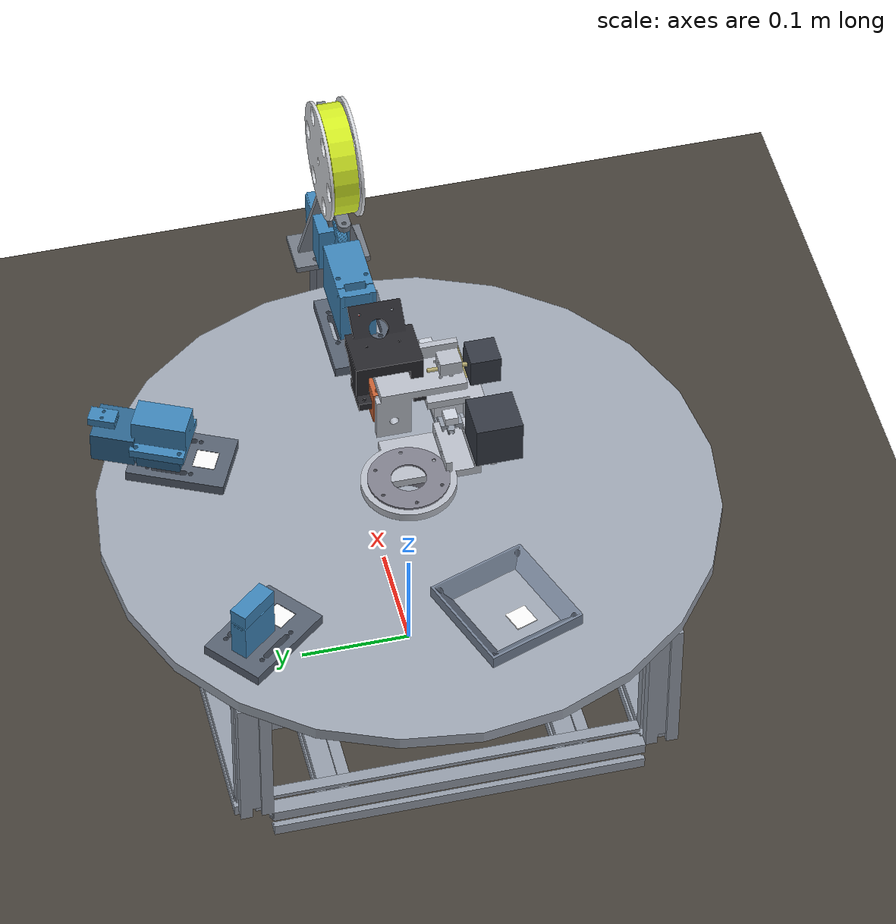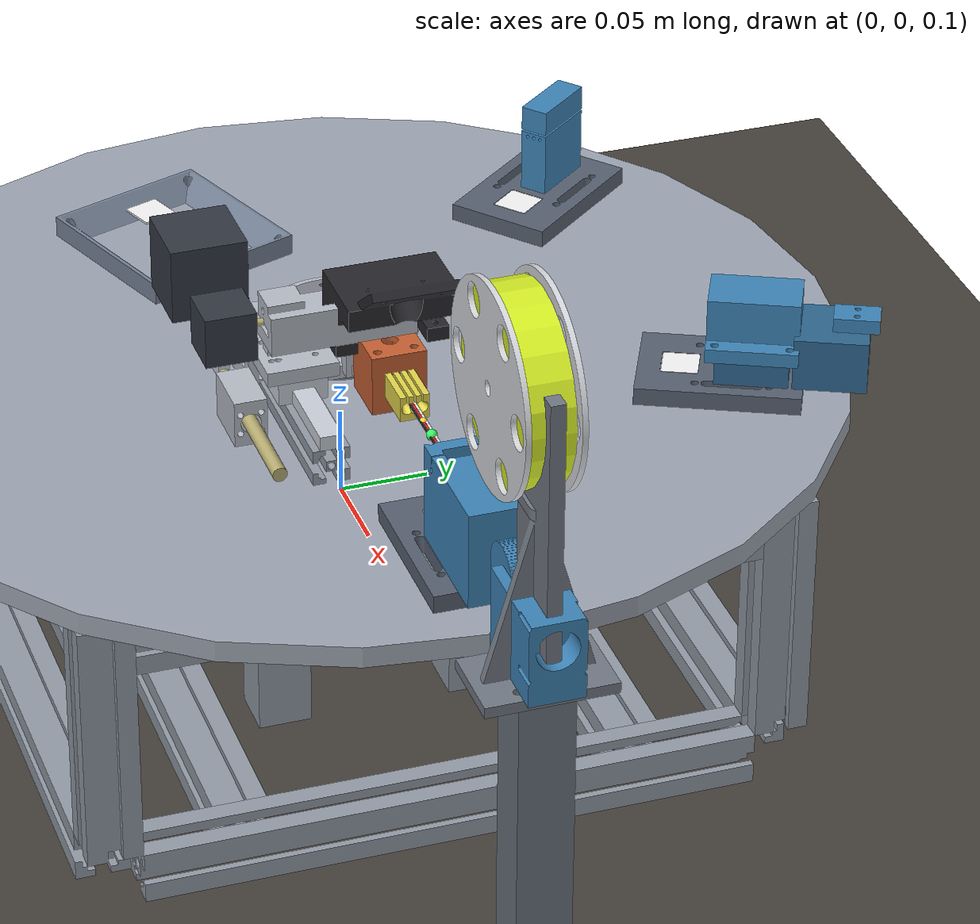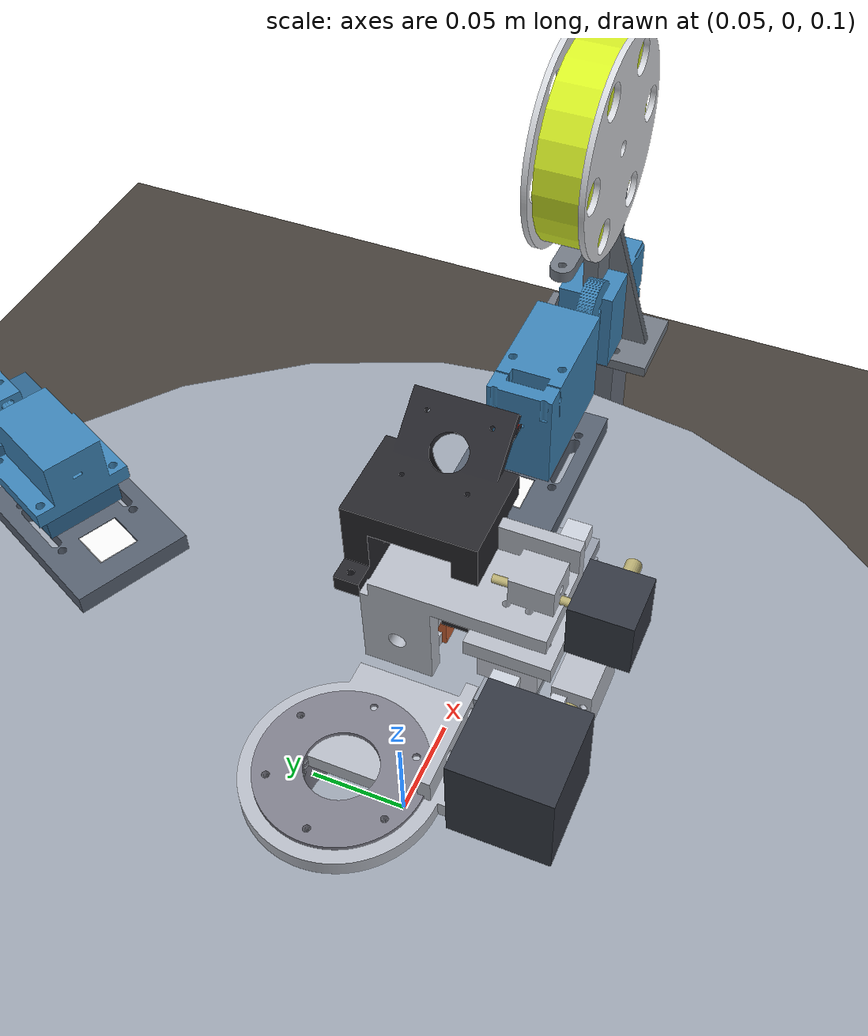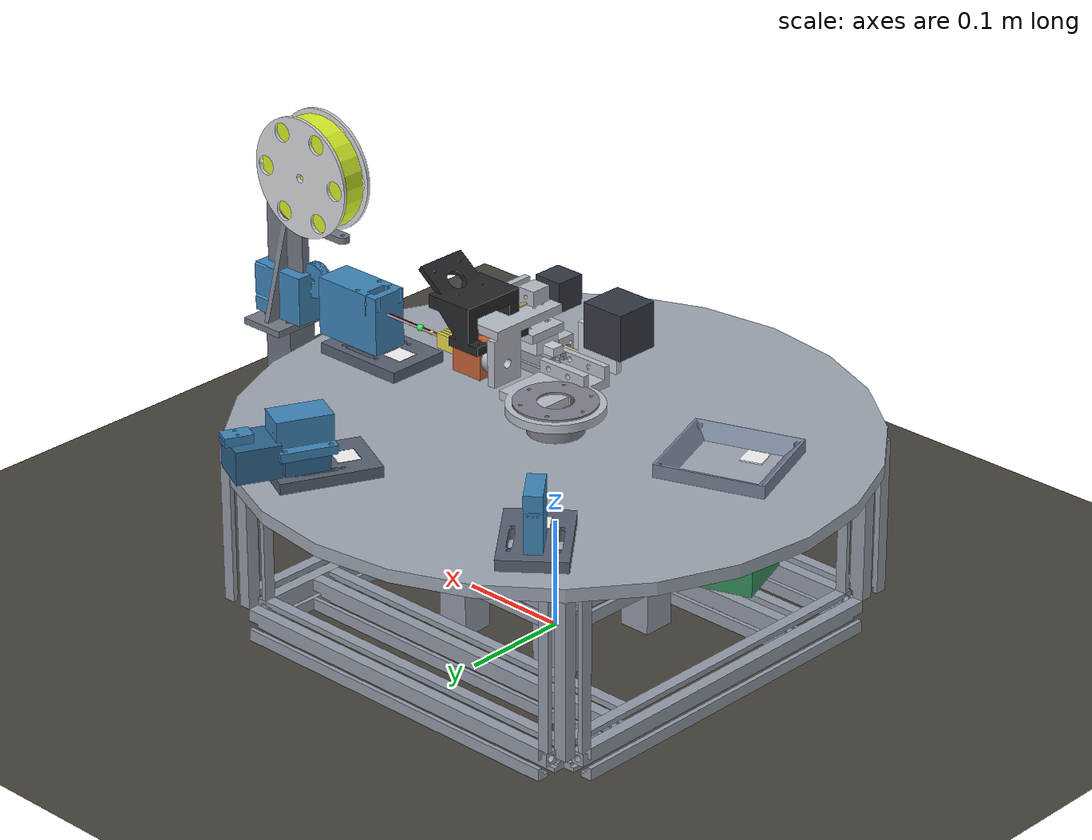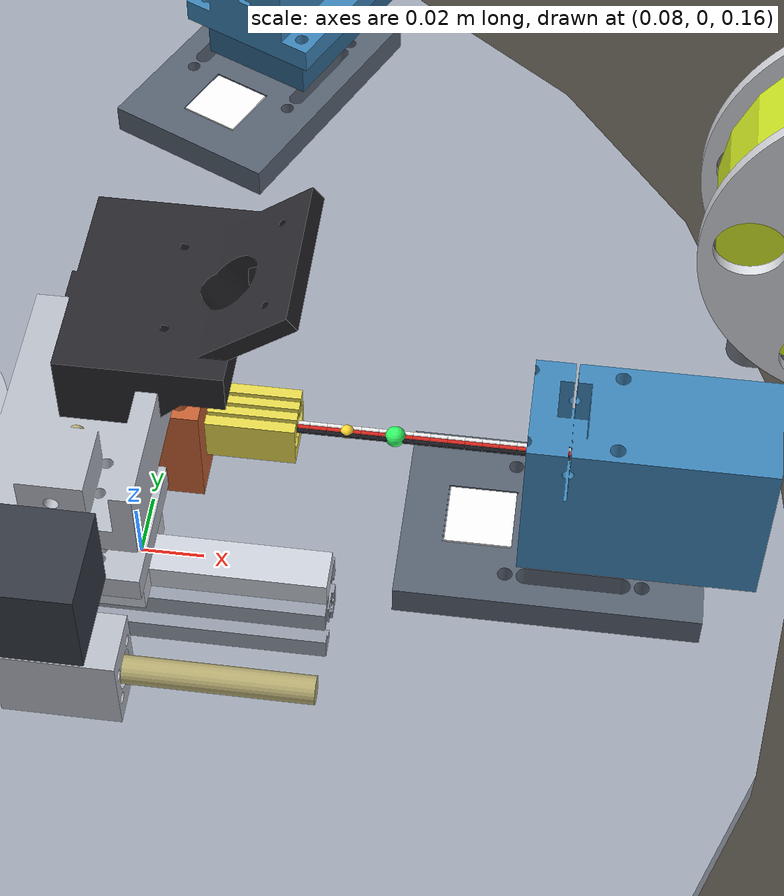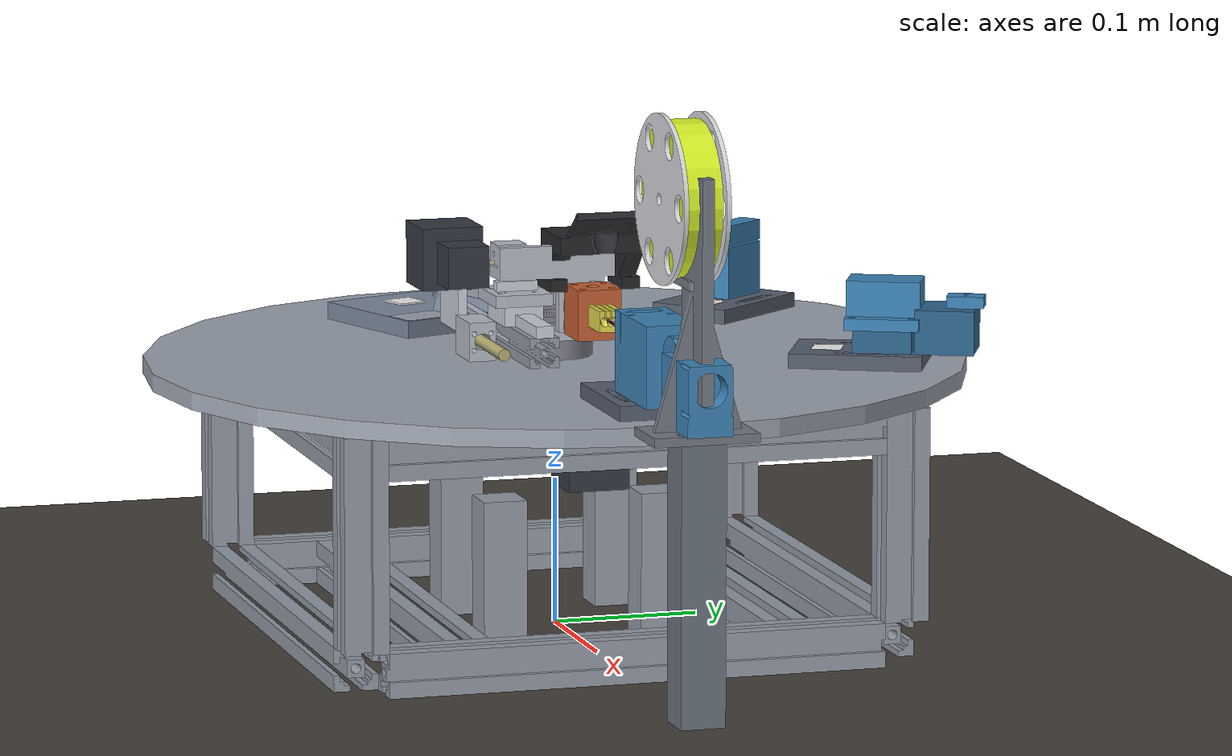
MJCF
<mujoco model="cablecell_roughin">
  <compiler angle="radian" autolimits="true" meshdir="../../cad/parts"/>
  <option integrator="implicitfast" timestep="0.002"/>

  <visual>
    <headlight ambient="0.45 0.45 0.45" diffuse="0.55 0.55 0.55"/>
    <global azimuth="130" elevation="-22" offwidth="1600" offheight="1000"/>
    <scale forcewidth="0.02" contactwidth="0.04" contactheight="0.02"/>
  </visual>

  <asset>
    <texture type="skybox" builtin="gradient" rgb1="0.30 0.38 0.48" rgb2="0.06 0.08 0.11"
      width="32" height="512"/>
    <texture name="bench_tex" type="2d" builtin="checker" rgb1="0.24 0.22 0.20"
      rgb2="0.30 0.28 0.25" width="300" height="300"/>
    <material name="bench_mat" texture="bench_tex" texrepeat="8 8" reflectance="0.03"/>
    <material name="frame_mat" rgba="0.42 0.45 0.50 1"/>
    <material name="deck_mat" rgba="0.62 0.65 0.70 1"/>
    <material name="press_mat" rgba="0.30 0.33 0.38 1"/>
    <material name="press_plate_mat" rgba="0.55 0.58 0.62 1"/>
    <material name="applicator_mat" rgba="0.80 0.55 0.15 1"/>
    <material name="station_mat" rgba="0.25 0.42 0.60 1"/>
    <material name="reject_mat" rgba="0.60 0.30 0.30 1"/>
    <!-- Printed parts read as printed; anything still grey is grey BECAUSE we
         do not know its shape, not because the modelling is unfinished. -->
    <material name="printed_mat" rgba="0.24 0.52 0.72 1"/>
    <material name="mount_mat" rgba="0.34 0.38 0.44 1"/>
    <material name="pedestal_mat" rgba="0.18 0.40 0.56 1"/>
    <material name="clamp_mat" rgba="0.78 0.38 0.20 1"/>
    <material name="extrusion_mat" rgba="0.58 0.61 0.66 1"/>
    <material name="rail_mat" rgba="0.80 0.82 0.86 1"/>
    <material name="unknown_mat" rgba="0.52 0.52 0.54 0.55"/>
    <material name="zstage_mat" rgba="0.35 0.55 0.42 1"/>
    <material name="rotor_mat" rgba="0.50 0.50 0.55 1"/>
    <material name="arm_mat" rgba="0.72 0.74 0.78 1"/>
    <material name="comb_mat" rgba="0.90 0.85 0.30 1"/>
    <material name="spool_mat" rgba="0.85 0.86 0.88 1"/>
    <material name="ribbon_mat" rgba="0.85 0.95 0.15 1"/>
    <material name="hanger_mat" rgba="0.45 0.48 0.52 1"/>
    <material name="camera_mat" rgba="0.15 0.15 0.17 1"/>
    <material name="cond_mat_0" rgba="0.10 0.10 0.12 1"/>
    <material name="cond_mat_1" rgba="0.85 0.15 0.12 1"/>
    <material name="cond_mat_2" rgba="0.95 0.95 0.95 1"/>
    <material name="chute_mat" rgba="0.45 0.50 0.58 1"/>
    <material name="collect_bin_mat" rgba="0.20 0.55 0.35 1"/>
    <material name="tag_mat" rgba="0.97 0.97 0.97 1"/>
    <material name="screw_mat" rgba="0.72 0.68 0.45 1"/>
    <material name="motor_mat" rgba="0.20 0.22 0.26 1"/>

    <!-- Real CAD geometry from cad/build_parts.py. Same layout.py dimensions
         drive both, so the printed part and the sim cannot disagree. STL is in
         millimetres; MuJoCo is in metres. -->
    <mesh name="comb_mesh" file="comb.stl" scale="0.001 0.001 0.001"/>
    <mesh name="spool_mesh" file="spool.stl" scale="0.001 0.001 0.001"/>
    <mesh name="spool_hanger_mesh" file="spool_hanger.stl" scale="0.001 0.001 0.001"/>
    <mesh name="dancer_arm_mesh" file="dancer_arm.stl" scale="0.001 0.001 0.001"/>
    <mesh name="feed_head_mesh" file="feed_head.stl" scale="0.001 0.001 0.001"/>
    <mesh name="measuring_wheel_mesh" file="measuring_wheel.stl" scale="0.001 0.001 0.001"/>
    <mesh name="splitting_wedge_mesh" file="splitting_wedge.stl" scale="0.001 0.001 0.001"/>
    <mesh name="spreader_plate_mesh" file="spreader_plate.stl" scale="0.001 0.001 0.001"/>
    <mesh name="z_platform_mesh" file="z_platform.stl" scale="0.001 0.001 0.001"/>
    <mesh name="spindle_shaft_mesh" file="spindle_shaft.stl" scale="0.001 0.001 0.001"/>
    <mesh name="radial_carriage_mesh" file="radial_carriage.stl" scale="0.001 0.001 0.001"/>
    <mesh name="wrist_mount_mesh" file="wrist_mount.stl" scale="0.001 0.001 0.001"/>
    <mesh name="camera_mount_mesh" file="camera_mount.stl" scale="0.001 0.001 0.001"/>
    <mesh name="drive_roller_block_mesh" file="drive_roller_block.stl" scale="0.001 0.001 0.001"/>
    <mesh name="station_mount_mesh" file="station_mount.stl" scale="0.001 0.001 0.001"/>
    <mesh name="cross_slide_carrier_mesh" file="cross_slide_carrier.stl" scale="0.001 0.001 0.001"/>
    <mesh name="body_clamp_mesh" file="body_clamp.stl" scale="0.001 0.001 0.001"/>
    <mesh name="strip_die_mesh" file="strip_die.stl" scale="0.001 0.001 0.001"/>
    <mesh name="rotor_plate_mesh" file="rotor_plate.stl" scale="0.001 0.001 0.001"/>
    <mesh name="drop_chute_mesh" file="drop_chute.stl" scale="0.001 0.001 0.001"/>
    <mesh name="ext2020_104_mesh" file="ext2020_104.stl" scale="0.001 0.001 0.001"/>
    <mesh name="ext3030_144_mesh" file="ext3030_144.stl" scale="0.001 0.001 0.001"/>
    <mesh name="ext3030_190_mesh" file="ext3030_190.stl" scale="0.001 0.001 0.001"/>
    <mesh name="ext3030_340_mesh" file="ext3030_340.stl" scale="0.001 0.001 0.001"/>
  </asset>

  <worldbody>
    <light pos="0.4 -0.5 1.6" dir="-0.2 0.25 -1" diffuse="0.6 0.6 0.6"/>
    <light pos="-0.5 0.4 1.2" dir="0.3 -0.25 -1" diffuse="0.35 0.35 0.35"/>

    <geom name="bench" type="plane" size="1.2 1.2 0.05" material="bench_mat"/>

    <!-- S4 press: stashed for the prototype. Still the deck-height datum. -->

    <!-- Frame and deck. Deck raised deliberately to collapse Z travel. -->
    <body name="deck_body">
    <geom name="deck" type="cylinder"
      pos="0 0 0.18"
      size="0.28 0.006"
      material="deck_mat" contype="5" conaffinity="3"/>
    </body>
    <body name="frame_body">
    <geom name="frame_leg_0" type="mesh" mesh="ext3030_144_mesh" pos="-0.185 -0.185 0.102" euler="0 1.5708 0" material="extrusion_mat" contype="1" conaffinity="1"/>
    <geom name="frame_leg_1" type="mesh" mesh="ext3030_144_mesh" pos="-0.185 0.185 0.102" euler="0 1.5708 0" material="extrusion_mat" contype="1" conaffinity="1"/>
    <geom name="frame_leg_2" type="mesh" mesh="ext3030_144_mesh" pos="0.185 -0.185 0.102" euler="0 1.5708 0" material="extrusion_mat" contype="1" conaffinity="1"/>
    <geom name="frame_leg_3" type="mesh" mesh="ext3030_144_mesh" pos="0.185 0.185 0.102" euler="0 1.5708 0" material="extrusion_mat" contype="1" conaffinity="1"/>
    <geom name="frame_bot_x_0" type="mesh" mesh="ext3030_340_mesh" pos="0 -0.185 0.015" euler="0 0 0" material="extrusion_mat" contype="1" conaffinity="1"/>
    <geom name="frame_bot_y_0" type="mesh" mesh="ext3030_340_mesh" pos="-0.185 0 0.015" euler="0 0 1.5708" material="extrusion_mat" contype="1" conaffinity="1"/>
    <geom name="frame_bot_x_1" type="mesh" mesh="ext3030_340_mesh" pos="0 0.185 0.015" euler="0 0 0" material="extrusion_mat" contype="1" conaffinity="1"/>
    <geom name="frame_bot_y_1" type="mesh" mesh="ext3030_340_mesh" pos="0.185 0 0.015" euler="0 0 1.5708" material="extrusion_mat" contype="1" conaffinity="1"/>
    <geom name="frame_top_x_0" type="mesh" mesh="ext3030_340_mesh" pos="0 -0.185 0.159" euler="0 0 0" material="extrusion_mat" contype="1" conaffinity="1"/>
    <geom name="frame_top_y_0" type="mesh" mesh="ext3030_340_mesh" pos="-0.185 0 0.159" euler="0 0 1.5708" material="extrusion_mat" contype="1" conaffinity="1"/>
    <geom name="frame_top_x_1" type="mesh" mesh="ext3030_340_mesh" pos="0 0.185 0.159" euler="0 0 0" material="extrusion_mat" contype="1" conaffinity="1"/>
    <geom name="frame_top_y_1" type="mesh" mesh="ext3030_340_mesh" pos="0.185 0 0.159" euler="0 0 1.5708" material="extrusion_mat" contype="1" conaffinity="1"/>
    <geom name="frame_cross_top_0" type="mesh" mesh="ext3030_340_mesh" pos="0 -0.11 0.159" euler="0 0 0" material="extrusion_mat" contype="1" conaffinity="1"/>
    <geom name="frame_cross_bot_0" type="mesh" mesh="ext3030_340_mesh" pos="0 -0.11 0.015" euler="0 0 0" material="extrusion_mat" contype="1" conaffinity="1"/>
    <geom name="frame_cross_top_1" type="mesh" mesh="ext3030_340_mesh" pos="0 0.11 0.159" euler="0 0 0" material="extrusion_mat" contype="1" conaffinity="1"/>
    <geom name="frame_cross_bot_1" type="mesh" mesh="ext3030_340_mesh" pos="0 0.11 0.015" euler="0 0 0" material="extrusion_mat" contype="1" conaffinity="1"/>
    </body>

    <geom name="s1_feed_mount" type="mesh" mesh="station_mount_mesh" pos="0.215 0 0.186" euler="0 0 0" material="mount_mat" contype="1" conaffinity="1"/>
    <geom name="s1_feed_feed_head" type="mesh" mesh="feed_head_mesh" pos="0.21 0 0.196" euler="0 0 0" material="printed_mat" contype="1" conaffinity="1"/>
    <geom name="s1_feed_tag" type="box" pos="0.186 0 0.1954" size="0.01 0.01 0.0006" euler="0 0 0" material="tag_mat" contype="1" conaffinity="1"/>
    <geom name="s2_slit_mount" type="mesh" mesh="station_mount_mesh" pos="0.0922956 0.194182 0.186" euler="0 0 1.1271" material="mount_mat" contype="1" conaffinity="1"/>
    <geom name="s2_slit_splitting_wedge" type="mesh" mesh="splitting_wedge_mesh" pos="0.0965884 0.203213 0.212" euler="0 0 1.1271" material="printed_mat" contype="1" conaffinity="1"/>
    <geom name="s2_slit_splitting_wedge_pedestal" type="box" pos="0.0965884 0.203213 0.204" size="0.02 0.02 0.008" euler="0 0 1.1271" material="pedestal_mat" contype="1" conaffinity="1"/>
    <geom name="s2_slit_spreader_plate" type="mesh" mesh="spreader_plate_mesh" pos="0.114618 0.241147 0.226" euler="0 0 1.1271" material="printed_mat" contype="1" conaffinity="1"/>
    <geom name="s2_slit_spreader_plate_pedestal" type="box" pos="0.114618 0.241147 0.211" size="0.02 0.02 0.015" euler="0 0 1.1271" material="pedestal_mat" contype="1" conaffinity="1"/>
    <geom name="s2_slit_tag" type="box" pos="0.0798464 0.16799 0.1954" size="0.01 0.01 0.0006" euler="0 0 1.1271" material="tag_mat" contype="1" conaffinity="1"/>
    <geom name="s3_strip_mount" type="mesh" mesh="station_mount_mesh" pos="-0.135758 0.166717 0.186" euler="0 0 2.2542" material="mount_mat" contype="1" conaffinity="1"/>
    <geom name="s3_strip_strip_die" type="mesh" mesh="strip_die_mesh" pos="-0.140178 0.172145 0.196" euler="0 0 2.2542" material="printed_mat" contype="1" conaffinity="1"/>
    <geom name="s3_strip_tag" type="box" pos="-0.117447 0.14423 0.1954" size="0.01 0.01 0.0006" euler="0 0 2.2542" material="tag_mat" contype="1" conaffinity="1"/>
    <!-- S6_DROP: collar over a deck hole, bin under. The cable hangs
         from R=130 and the deck is what is under it — a
         funnel out at the bolt circle would have missed by 68 mm. -->
    <geom name="s6_drop_chute" type="mesh" mesh="drop_chute_mesh" pos="-0.14824 -0.0527218 0.186" euler="0 0 3.48329" material="chute_mat" contype="1" conaffinity="1"/>
    <geom name="s6_drop_bin" type="box" pos="-0.14824 -0.0527218 0.129" size="0.0346637 0.032 0.045" euler="0 0 3.48329" material="collect_bin_mat" contype="1" conaffinity="1"/>
    <geom name="s6_drop_tag" type="box" pos="-0.169593 -0.0603162 0.1974" size="0.01 0.01 0.0006" euler="0 0 3.48329" material="tag_mat" contype="1" conaffinity="1"/>

    <!-- S1's spool + hanger + dancer, off-deck outboard of station 1. -->
    <geom name="spool" type="mesh" mesh="spool_mesh" pos="0.29 0.0155 0.336" euler="1.5708 0 0" material="spool_mat" contype="1" conaffinity="1"/>
    <geom name="spool_ribbon" type="cylinder" pos="0.29 0 0.336" size="0.051 0.0115" euler="1.5708 0 0" material="ribbon_mat" contype="1" conaffinity="1"/>
    <geom name="spool_post" type="box" pos="0.324 0 0.093" size="0.015 0.015 0.093" material="frame_mat" contype="1" conaffinity="1"/>
    <geom name="spool_hanger" type="mesh" mesh="spool_hanger_mesh" pos="0.324 0 0.186" euler="0 0 1.5708" material="hanger_mat" contype="1" conaffinity="1"/>
    <geom name="dancer_arm" type="mesh" mesh="dancer_arm_mesh" pos="0.324 0 0.282" euler="0 0 3.14159" material="hanger_mat" contype="1" conaffinity="1"/>
    <geom name="drive_roller_block" type="mesh" mesh="drive_roller_block_mesh" pos="0.324 0 0.192" euler="0 0 3.14159" material="printed_mat" contype="1" conaffinity="1"/>
    <geom name="measuring_wheel" type="mesh" mesh="measuring_wheel_mesh" pos="0.294 0 0.232" euler="1.5708 0 0" material="printed_mat" contype="1" conaffinity="1"/>

    <body name="post_body">
    <geom name="z_pedestal_0" type="box" pos="-0.055 -0.055 0.05" size="0.015 0.015 0.05" material="extrusion_mat" contype="1" conaffinity="1"/>
    <geom name="z_pedestal_1" type="box" pos="-0.055 0.055 0.05" size="0.015 0.015 0.05" material="extrusion_mat" contype="1" conaffinity="1"/>
    <geom name="z_pedestal_2" type="box" pos="0.055 -0.055 0.05" size="0.015 0.015 0.05" material="extrusion_mat" contype="1" conaffinity="1"/>
    <geom name="z_pedestal_3" type="box" pos="0.055 0.055 0.05" size="0.015 0.015 0.05" material="extrusion_mat" contype="1" conaffinity="1"/>
    </body>

    <body name="stock_0_0" pos="0.2 -0.0014 0.23" euler="0 0 0">
      <joint name="stock_0_0_z" type="hinge" axis="0 0 1" stiffness="0.188574" damping="0.0094287" armature="1e-06"/>
      <joint name="stock_0_0_y" type="hinge" axis="0 1 0" stiffness="0.188574" damping="0.0094287" armature="1e-06"/>
      <geom name="stock_0_0" type="capsule" fromto="0 0 0 0.005 0 0" size="0.0007" material="cond_mat_0" contype="2" conaffinity="4" mass="2.73333e-05"/>
      <body name="stock_0_1" pos="0.005 0 0">
        <joint name="stock_0_1_z" type="hinge" axis="0 0 1" stiffness="0.188574" damping="0.0094287" armature="1e-06"/>
        <joint name="stock_0_1_y" type="hinge" axis="0 1 0" stiffness="0.188574" damping="0.0094287" armature="1e-06"/>
        <geom name="stock_0_1" type="capsule" fromto="0 0 0 0.005 0 0" size="0.0007" material="cond_mat_0" contype="2" conaffinity="4" mass="2.73333e-05"/>
        <body name="stock_0_2" pos="0.005 0 0">
          <joint name="stock_0_2_z" type="hinge" axis="0 0 1" stiffness="0.188574" damping="0.0094287" armature="1e-06"/>
          <joint name="stock_0_2_y" type="hinge" axis="0 1 0" stiffness="0.188574" damping="0.0094287" armature="1e-06"/>
          <geom name="stock_0_2" type="capsule" fromto="0 0 0 0.005 0 0" size="0.0007" material="cond_mat_0" contype="2" conaffinity="4" mass="2.73333e-05"/>
          <body name="stock_0_3" pos="0.005 0 0">
            <joint name="stock_0_3_z" type="hinge" axis="0 0 1" stiffness="0.188574" damping="0.0094287" armature="1e-06"/>
            <joint name="stock_0_3_y" type="hinge" axis="0 1 0" stiffness="0.188574" damping="0.0094287" armature="1e-06"/>
            <geom name="stock_0_3" type="capsule" fromto="0 0 0 0.005 0 0" size="0.0007" material="cond_mat_0" contype="2" conaffinity="4" mass="2.73333e-05"/>
            <body name="stock_0_4" pos="0.005 0 0">
              <joint name="stock_0_4_z" type="hinge" axis="0 0 1" stiffness="0.188574" damping="0.0094287" armature="1e-06"/>
              <joint name="stock_0_4_y" type="hinge" axis="0 1 0" stiffness="0.188574" damping="0.0094287" armature="1e-06"/>
              <geom name="stock_0_4" type="capsule" fromto="0 0 0 0.005 0 0" size="0.0007" material="cond_mat_0" contype="2" conaffinity="4" mass="2.73333e-05"/>
              <body name="stock_0_5" pos="0.005 0 0">
                <joint name="stock_0_5_z" type="hinge" axis="0 0 1" stiffness="0.188574" damping="0.0094287" armature="1e-06"/>
                <joint name="stock_0_5_y" type="hinge" axis="0 1 0" stiffness="0.188574" damping="0.0094287" armature="1e-06"/>
                <geom name="stock_0_5" type="capsule" fromto="0 0 0 0.005 0 0" size="0.0007" material="cond_mat_0" contype="2" conaffinity="4" mass="2.73333e-05"/>
              </body>
            </body>
          </body>
        </body>
      </body>
    </body>
    <body name="rib_0_0" pos="0.2 -0.0014 0.23" euler="0 0 3.14159">
      <freejoint name="rib_0_free"/>
      <geom name="rib_0_0" type="capsule" fromto="0 0 0 0.005 0 0" size="0.0007" material="cond_mat_0" contype="2" conaffinity="4" mass="2.73333e-05"/>
      <body name="rib_0_1" pos="0.005 0 0">
        <joint name="rib_0_1_z" type="hinge" axis="0 0 1" stiffness="0.188574" damping="0.0094287" armature="1e-06"/>
        <joint name="rib_0_1_y" type="hinge" axis="0 1 0" stiffness="0.188574" damping="0.0094287" armature="1e-06"/>
        <geom name="rib_0_1" type="capsule" fromto="0 0 0 0.005 0 0" size="0.0007" material="cond_mat_0" contype="2" conaffinity="4" mass="2.73333e-05"/>
        <body name="rib_0_2" pos="0.005 0 0">
          <joint name="rib_0_2_z" type="hinge" axis="0 0 1" stiffness="0.188574" damping="0.0094287" armature="1e-06"/>
          <joint name="rib_0_2_y" type="hinge" axis="0 1 0" stiffness="0.188574" damping="0.0094287" armature="1e-06"/>
          <geom name="rib_0_2" type="capsule" fromto="0 0 0 0.005 0 0" size="0.0007" material="cond_mat_0" contype="2" conaffinity="4" mass="2.73333e-05"/>
          <body name="rib_0_3" pos="0.005 0 0">
            <joint name="rib_0_3_z" type="hinge" axis="0 0 1" stiffness="0.188574" damping="0.0094287" armature="1e-06"/>
            <joint name="rib_0_3_y" type="hinge" axis="0 1 0" stiffness="0.188574" damping="0.0094287" armature="1e-06"/>
            <geom name="rib_0_3" type="capsule" fromto="0 0 0 0.005 0 0" size="0.0007" material="cond_mat_0" contype="2" conaffinity="4" mass="2.73333e-05"/>
            <body name="rib_0_4" pos="0.005 0 0">
              <joint name="rib_0_4_z" type="hinge" axis="0 0 1" stiffness="0.188574" damping="0.0094287" armature="1e-06"/>
              <joint name="rib_0_4_y" type="hinge" axis="0 1 0" stiffness="0.188574" damping="0.0094287" armature="1e-06"/>
              <geom name="rib_0_4" type="capsule" fromto="0 0 0 0.005 0 0" size="0.0007" material="cond_mat_0" contype="2" conaffinity="4" mass="2.73333e-05"/>
              <body name="rib_0_5" pos="0.005 0 0">
                <joint name="rib_0_5_z" type="hinge" axis="0 0 1" stiffness="0.188574" damping="0.0094287" armature="1e-06"/>
                <joint name="rib_0_5_y" type="hinge" axis="0 1 0" stiffness="0.188574" damping="0.0094287" armature="1e-06"/>
                <geom name="rib_0_5" type="capsule" fromto="0 0 0 0.005 0 0" size="0.0007" material="cond_mat_0" contype="2" conaffinity="4" mass="2.73333e-05"/>
                <body name="rib_0_6" pos="0.005 0 0">
                  <joint name="rib_0_6_z" type="hinge" axis="0 0 1" stiffness="0.188574" damping="0.0094287" armature="1e-06"/>
                  <joint name="rib_0_6_y" type="hinge" axis="0 1 0" stiffness="0.188574" damping="0.0094287" armature="1e-06"/>
                  <geom name="rib_0_6" type="capsule" fromto="0 0 0 0.005 0 0" size="0.0007" material="cond_mat_0" contype="2" conaffinity="4" mass="2.73333e-05"/>
                  <body name="rib_0_7" pos="0.005 0 0">
                    <joint name="rib_0_7_z" type="hinge" axis="0 0 1" stiffness="0.188574" damping="0.0094287" armature="1e-06"/>
                    <joint name="rib_0_7_y" type="hinge" axis="0 1 0" stiffness="0.188574" damping="0.0094287" armature="1e-06"/>
                    <geom name="rib_0_7" type="capsule" fromto="0 0 0 0.005 0 0" size="0.0007" material="cond_mat_0" contype="2" conaffinity="4" mass="2.73333e-05"/>
                    <body name="rib_0_8" pos="0.005 0 0">
                      <joint name="rib_0_8_z" type="hinge" axis="0 0 1" stiffness="0.188574" damping="0.0094287" armature="1e-06"/>
                      <joint name="rib_0_8_y" type="hinge" axis="0 1 0" stiffness="0.188574" damping="0.0094287" armature="1e-06"/>
                      <geom name="rib_0_8" type="capsule" fromto="0 0 0 0.005 0 0" size="0.0007" material="cond_mat_0" contype="2" conaffinity="4" mass="2.73333e-05"/>
                      <body name="rib_0_9" pos="0.005 0 0">
                        <joint name="rib_0_9_z" type="hinge" axis="0 0 1" stiffness="0.188574" damping="0.0094287" armature="1e-06"/>
                        <joint name="rib_0_9_y" type="hinge" axis="0 1 0" stiffness="0.188574" damping="0.0094287" armature="1e-06"/>
                        <geom name="rib_0_9" type="capsule" fromto="0 0 0 0.005 0 0" size="0.0007" material="cond_mat_0" contype="2" conaffinity="4" mass="2.73333e-05"/>
                        <body name="rib_0_10" pos="0.005 0 0">
                          <joint name="rib_0_10_z" type="hinge" axis="0 0 1" stiffness="0.188574" damping="0.0094287" armature="1e-06"/>
                          <joint name="rib_0_10_y" type="hinge" axis="0 1 0" stiffness="0.188574" damping="0.0094287" armature="1e-06"/>
                          <geom name="rib_0_10" type="capsule" fromto="0 0 0 0.005 0 0" size="0.0007" material="cond_mat_0" contype="2" conaffinity="4" mass="2.73333e-05"/>
                          <body name="rib_0_11" pos="0.005 0 0">
                            <joint name="rib_0_11_z" type="hinge" axis="0 0 1" stiffness="0.188574" damping="0.0094287" armature="1e-06"/>
                            <joint name="rib_0_11_y" type="hinge" axis="0 1 0" stiffness="0.188574" damping="0.0094287" armature="1e-06"/>
                            <geom name="rib_0_11" type="capsule" fromto="0 0 0 0.005 0 0" size="0.0007" material="cond_mat_0" contype="2" conaffinity="4" mass="2.73333e-05"/>
                            <body name="rib_0_12" pos="0.005 0 0">
                              <joint name="rib_0_12_z" type="hinge" axis="0 0 1" stiffness="0.188574" damping="0.0094287" armature="1e-06"/>
                              <joint name="rib_0_12_y" type="hinge" axis="0 1 0" stiffness="0.188574" damping="0.0094287" armature="1e-06"/>
                              <geom name="rib_0_12" type="capsule" fromto="0 0 0 0.005 0 0" size="0.0007" material="cond_mat_0" contype="2" conaffinity="4" mass="2.73333e-05"/>
                              <body name="rib_0_13" pos="0.005 0 0">
                                <joint name="rib_0_13_z" type="hinge" axis="0 0 1" stiffness="0.188574" damping="0.0094287" armature="1e-06"/>
                                <joint name="rib_0_13_y" type="hinge" axis="0 1 0" stiffness="0.188574" damping="0.0094287" armature="1e-06"/>
                                <geom name="rib_0_13" type="capsule" fromto="0 0 0 0.005 0 0" size="0.0007" material="cond_mat_0" contype="2" conaffinity="4" mass="2.73333e-05"/>
                                <body name="rib_0_14" pos="0.005 0 0">
                                  <joint name="rib_0_14_z" type="hinge" axis="0 0 1" stiffness="0.188574" damping="0.0094287" armature="1e-06"/>
                                  <joint name="rib_0_14_y" type="hinge" axis="0 1 0" stiffness="0.188574" damping="0.0094287" armature="1e-06"/>
                                  <geom name="rib_0_14" type="capsule" fromto="0 0 0 0.005 0 0" size="0.0007" material="cond_mat_0" contype="2" conaffinity="4" mass="2.73333e-05"/>
                                  <body name="rib_0_15" pos="0.005 0 0">
                                    <joint name="rib_0_15_z" type="hinge" axis="0 0 1" stiffness="0.188574" damping="0.0094287" armature="1e-06"/>
                                    <joint name="rib_0_15_y" type="hinge" axis="0 1 0" stiffness="0.188574" damping="0.0094287" armature="1e-06"/>
                                    <geom name="rib_0_15" type="capsule" fromto="0 0 0 0.005 0 0" size="0.0007" material="cond_mat_0" contype="2" conaffinity="4" mass="2.73333e-05"/>
                                    <body name="rib_0_16" pos="0.005 0 0">
                                      <joint name="rib_0_16_z" type="hinge" axis="0 0 1" stiffness="0.188574" damping="0.0094287" armature="1e-06"/>
                                      <joint name="rib_0_16_y" type="hinge" axis="0 1 0" stiffness="0.188574" damping="0.0094287" armature="1e-06"/>
                                      <geom name="rib_0_16" type="capsule" fromto="0 0 0 0.005 0 0" size="0.0007" material="cond_mat_0" contype="2" conaffinity="4" mass="2.73333e-05"/>
                                      <body name="rib_0_17" pos="0.005 0 0">
                                        <joint name="rib_0_17_z" type="hinge" axis="0 0 1" stiffness="0.188574" damping="0.0094287" armature="1e-06"/>
                                        <joint name="rib_0_17_y" type="hinge" axis="0 1 0" stiffness="0.188574" damping="0.0094287" armature="1e-06"/>
                                        <geom name="rib_0_17" type="capsule" fromto="0 0 0 0.005 0 0" size="0.0007" material="cond_mat_0" contype="2" conaffinity="4" mass="2.73333e-05"/>
                                      </body>
                                    </body>
                                  </body>
                                </body>
                              </body>
                            </body>
                          </body>
                        </body>
                      </body>
                    </body>
                  </body>
                </body>
              </body>
            </body>
          </body>
        </body>
      </body>
    </body>
    <body name="stock_1_0" pos="0.2 0 0.23" euler="0 0 0">
      <joint name="stock_1_0_z" type="hinge" axis="0 0 1" stiffness="0.188574" damping="0.0094287" armature="1e-06"/>
      <joint name="stock_1_0_y" type="hinge" axis="0 1 0" stiffness="0.188574" damping="0.0094287" armature="1e-06"/>
      <geom name="stock_1_0" type="capsule" fromto="0 0 0 0.005 0 0" size="0.0007" material="cond_mat_1" contype="2" conaffinity="4" mass="2.73333e-05"/>
      <body name="stock_1_1" pos="0.005 0 0">
        <joint name="stock_1_1_z" type="hinge" axis="0 0 1" stiffness="0.188574" damping="0.0094287" armature="1e-06"/>
        <joint name="stock_1_1_y" type="hinge" axis="0 1 0" stiffness="0.188574" damping="0.0094287" armature="1e-06"/>
        <geom name="stock_1_1" type="capsule" fromto="0 0 0 0.005 0 0" size="0.0007" material="cond_mat_1" contype="2" conaffinity="4" mass="2.73333e-05"/>
        <body name="stock_1_2" pos="0.005 0 0">
          <joint name="stock_1_2_z" type="hinge" axis="0 0 1" stiffness="0.188574" damping="0.0094287" armature="1e-06"/>
          <joint name="stock_1_2_y" type="hinge" axis="0 1 0" stiffness="0.188574" damping="0.0094287" armature="1e-06"/>
          <geom name="stock_1_2" type="capsule" fromto="0 0 0 0.005 0 0" size="0.0007" material="cond_mat_1" contype="2" conaffinity="4" mass="2.73333e-05"/>
          <body name="stock_1_3" pos="0.005 0 0">
            <joint name="stock_1_3_z" type="hinge" axis="0 0 1" stiffness="0.188574" damping="0.0094287" armature="1e-06"/>
            <joint name="stock_1_3_y" type="hinge" axis="0 1 0" stiffness="0.188574" damping="0.0094287" armature="1e-06"/>
            <geom name="stock_1_3" type="capsule" fromto="0 0 0 0.005 0 0" size="0.0007" material="cond_mat_1" contype="2" conaffinity="4" mass="2.73333e-05"/>
            <body name="stock_1_4" pos="0.005 0 0">
              <joint name="stock_1_4_z" type="hinge" axis="0 0 1" stiffness="0.188574" damping="0.0094287" armature="1e-06"/>
              <joint name="stock_1_4_y" type="hinge" axis="0 1 0" stiffness="0.188574" damping="0.0094287" armature="1e-06"/>
              <geom name="stock_1_4" type="capsule" fromto="0 0 0 0.005 0 0" size="0.0007" material="cond_mat_1" contype="2" conaffinity="4" mass="2.73333e-05"/>
              <body name="stock_1_5" pos="0.005 0 0">
                <joint name="stock_1_5_z" type="hinge" axis="0 0 1" stiffness="0.188574" damping="0.0094287" armature="1e-06"/>
                <joint name="stock_1_5_y" type="hinge" axis="0 1 0" stiffness="0.188574" damping="0.0094287" armature="1e-06"/>
                <geom name="stock_1_5" type="capsule" fromto="0 0 0 0.005 0 0" size="0.0007" material="cond_mat_1" contype="2" conaffinity="4" mass="2.73333e-05"/>
              </body>
            </body>
          </body>
        </body>
      </body>
    </body>
    <body name="rib_1_0" pos="0.2 0 0.23" euler="0 0 3.14159">
      <freejoint name="rib_1_free"/>
      <geom name="rib_1_0" type="capsule" fromto="0 0 0 0.005 0 0" size="0.0007" material="cond_mat_1" contype="2" conaffinity="4" mass="2.73333e-05"/>
      <body name="rib_1_1" pos="0.005 0 0">
        <joint name="rib_1_1_z" type="hinge" axis="0 0 1" stiffness="0.188574" damping="0.0094287" armature="1e-06"/>
        <joint name="rib_1_1_y" type="hinge" axis="0 1 0" stiffness="0.188574" damping="0.0094287" armature="1e-06"/>
        <geom name="rib_1_1" type="capsule" fromto="0 0 0 0.005 0 0" size="0.0007" material="cond_mat_1" contype="2" conaffinity="4" mass="2.73333e-05"/>
        <body name="rib_1_2" pos="0.005 0 0">
          <joint name="rib_1_2_z" type="hinge" axis="0 0 1" stiffness="0.188574" damping="0.0094287" armature="1e-06"/>
          <joint name="rib_1_2_y" type="hinge" axis="0 1 0" stiffness="0.188574" damping="0.0094287" armature="1e-06"/>
          <geom name="rib_1_2" type="capsule" fromto="0 0 0 0.005 0 0" size="0.0007" material="cond_mat_1" contype="2" conaffinity="4" mass="2.73333e-05"/>
          <body name="rib_1_3" pos="0.005 0 0">
            <joint name="rib_1_3_z" type="hinge" axis="0 0 1" stiffness="0.188574" damping="0.0094287" armature="1e-06"/>
            <joint name="rib_1_3_y" type="hinge" axis="0 1 0" stiffness="0.188574" damping="0.0094287" armature="1e-06"/>
            <geom name="rib_1_3" type="capsule" fromto="0 0 0 0.005 0 0" size="0.0007" material="cond_mat_1" contype="2" conaffinity="4" mass="2.73333e-05"/>
            <body name="rib_1_4" pos="0.005 0 0">
              <joint name="rib_1_4_z" type="hinge" axis="0 0 1" stiffness="0.188574" damping="0.0094287" armature="1e-06"/>
              <joint name="rib_1_4_y" type="hinge" axis="0 1 0" stiffness="0.188574" damping="0.0094287" armature="1e-06"/>
              <geom name="rib_1_4" type="capsule" fromto="0 0 0 0.005 0 0" size="0.0007" material="cond_mat_1" contype="2" conaffinity="4" mass="2.73333e-05"/>
              <body name="rib_1_5" pos="0.005 0 0">
                <joint name="rib_1_5_z" type="hinge" axis="0 0 1" stiffness="0.188574" damping="0.0094287" armature="1e-06"/>
                <joint name="rib_1_5_y" type="hinge" axis="0 1 0" stiffness="0.188574" damping="0.0094287" armature="1e-06"/>
                <geom name="rib_1_5" type="capsule" fromto="0 0 0 0.005 0 0" size="0.0007" material="cond_mat_1" contype="2" conaffinity="4" mass="2.73333e-05"/>
                <body name="rib_1_6" pos="0.005 0 0">
                  <joint name="rib_1_6_z" type="hinge" axis="0 0 1" stiffness="0.188574" damping="0.0094287" armature="1e-06"/>
                  <joint name="rib_1_6_y" type="hinge" axis="0 1 0" stiffness="0.188574" damping="0.0094287" armature="1e-06"/>
                  <geom name="rib_1_6" type="capsule" fromto="0 0 0 0.005 0 0" size="0.0007" material="cond_mat_1" contype="2" conaffinity="4" mass="2.73333e-05"/>
                  <body name="rib_1_7" pos="0.005 0 0">
                    <joint name="rib_1_7_z" type="hinge" axis="0 0 1" stiffness="0.188574" damping="0.0094287" armature="1e-06"/>
                    <joint name="rib_1_7_y" type="hinge" axis="0 1 0" stiffness="0.188574" damping="0.0094287" armature="1e-06"/>
                    <geom name="rib_1_7" type="capsule" fromto="0 0 0 0.005 0 0" size="0.0007" material="cond_mat_1" contype="2" conaffinity="4" mass="2.73333e-05"/>
                    <body name="rib_1_8" pos="0.005 0 0">
                      <joint name="rib_1_8_z" type="hinge" axis="0 0 1" stiffness="0.188574" damping="0.0094287" armature="1e-06"/>
                      <joint name="rib_1_8_y" type="hinge" axis="0 1 0" stiffness="0.188574" damping="0.0094287" armature="1e-06"/>
                      <geom name="rib_1_8" type="capsule" fromto="0 0 0 0.005 0 0" size="0.0007" material="cond_mat_1" contype="2" conaffinity="4" mass="2.73333e-05"/>
                      <body name="rib_1_9" pos="0.005 0 0">
                        <joint name="rib_1_9_z" type="hinge" axis="0 0 1" stiffness="0.188574" damping="0.0094287" armature="1e-06"/>
                        <joint name="rib_1_9_y" type="hinge" axis="0 1 0" stiffness="0.188574" damping="0.0094287" armature="1e-06"/>
                        <geom name="rib_1_9" type="capsule" fromto="0 0 0 0.005 0 0" size="0.0007" material="cond_mat_1" contype="2" conaffinity="4" mass="2.73333e-05"/>
                        <body name="rib_1_10" pos="0.005 0 0">
                          <joint name="rib_1_10_z" type="hinge" axis="0 0 1" stiffness="0.188574" damping="0.0094287" armature="1e-06"/>
                          <joint name="rib_1_10_y" type="hinge" axis="0 1 0" stiffness="0.188574" damping="0.0094287" armature="1e-06"/>
                          <geom name="rib_1_10" type="capsule" fromto="0 0 0 0.005 0 0" size="0.0007" material="cond_mat_1" contype="2" conaffinity="4" mass="2.73333e-05"/>
                          <body name="rib_1_11" pos="0.005 0 0">
                            <joint name="rib_1_11_z" type="hinge" axis="0 0 1" stiffness="0.188574" damping="0.0094287" armature="1e-06"/>
                            <joint name="rib_1_11_y" type="hinge" axis="0 1 0" stiffness="0.188574" damping="0.0094287" armature="1e-06"/>
                            <geom name="rib_1_11" type="capsule" fromto="0 0 0 0.005 0 0" size="0.0007" material="cond_mat_1" contype="2" conaffinity="4" mass="2.73333e-05"/>
                            <body name="rib_1_12" pos="0.005 0 0">
                              <joint name="rib_1_12_z" type="hinge" axis="0 0 1" stiffness="0.188574" damping="0.0094287" armature="1e-06"/>
                              <joint name="rib_1_12_y" type="hinge" axis="0 1 0" stiffness="0.188574" damping="0.0094287" armature="1e-06"/>
                              <geom name="rib_1_12" type="capsule" fromto="0 0 0 0.005 0 0" size="0.0007" material="cond_mat_1" contype="2" conaffinity="4" mass="2.73333e-05"/>
                              <body name="rib_1_13" pos="0.005 0 0">
                                <joint name="rib_1_13_z" type="hinge" axis="0 0 1" stiffness="0.188574" damping="0.0094287" armature="1e-06"/>
                                <joint name="rib_1_13_y" type="hinge" axis="0 1 0" stiffness="0.188574" damping="0.0094287" armature="1e-06"/>
                                <geom name="rib_1_13" type="capsule" fromto="0 0 0 0.005 0 0" size="0.0007" material="cond_mat_1" contype="2" conaffinity="4" mass="2.73333e-05"/>
                                <body name="rib_1_14" pos="0.005 0 0">
                                  <joint name="rib_1_14_z" type="hinge" axis="0 0 1" stiffness="0.188574" damping="0.0094287" armature="1e-06"/>
                                  <joint name="rib_1_14_y" type="hinge" axis="0 1 0" stiffness="0.188574" damping="0.0094287" armature="1e-06"/>
                                  <geom name="rib_1_14" type="capsule" fromto="0 0 0 0.005 0 0" size="0.0007" material="cond_mat_1" contype="2" conaffinity="4" mass="2.73333e-05"/>
                                  <body name="rib_1_15" pos="0.005 0 0">
                                    <joint name="rib_1_15_z" type="hinge" axis="0 0 1" stiffness="0.188574" damping="0.0094287" armature="1e-06"/>
                                    <joint name="rib_1_15_y" type="hinge" axis="0 1 0" stiffness="0.188574" damping="0.0094287" armature="1e-06"/>
                                    <geom name="rib_1_15" type="capsule" fromto="0 0 0 0.005 0 0" size="0.0007" material="cond_mat_1" contype="2" conaffinity="4" mass="2.73333e-05"/>
                                    <body name="rib_1_16" pos="0.005 0 0">
                                      <joint name="rib_1_16_z" type="hinge" axis="0 0 1" stiffness="0.188574" damping="0.0094287" armature="1e-06"/>
                                      <joint name="rib_1_16_y" type="hinge" axis="0 1 0" stiffness="0.188574" damping="0.0094287" armature="1e-06"/>
                                      <geom name="rib_1_16" type="capsule" fromto="0 0 0 0.005 0 0" size="0.0007" material="cond_mat_1" contype="2" conaffinity="4" mass="2.73333e-05"/>
                                      <body name="rib_1_17" pos="0.005 0 0">
                                        <joint name="rib_1_17_z" type="hinge" axis="0 0 1" stiffness="0.188574" damping="0.0094287" armature="1e-06"/>
                                        <joint name="rib_1_17_y" type="hinge" axis="0 1 0" stiffness="0.188574" damping="0.0094287" armature="1e-06"/>
                                        <geom name="rib_1_17" type="capsule" fromto="0 0 0 0.005 0 0" size="0.0007" material="cond_mat_1" contype="2" conaffinity="4" mass="2.73333e-05"/>
                                      </body>
                                    </body>
                                  </body>
                                </body>
                              </body>
                            </body>
                          </body>
                        </body>
                      </body>
                    </body>
                  </body>
                </body>
              </body>
            </body>
          </body>
        </body>
      </body>
    </body>
    <body name="stock_2_0" pos="0.2 0.0014 0.23" euler="0 0 0">
      <joint name="stock_2_0_z" type="hinge" axis="0 0 1" stiffness="0.188574" damping="0.0094287" armature="1e-06"/>
      <joint name="stock_2_0_y" type="hinge" axis="0 1 0" stiffness="0.188574" damping="0.0094287" armature="1e-06"/>
      <geom name="stock_2_0" type="capsule" fromto="0 0 0 0.005 0 0" size="0.0007" material="cond_mat_2" contype="2" conaffinity="4" mass="2.73333e-05"/>
      <body name="stock_2_1" pos="0.005 0 0">
        <joint name="stock_2_1_z" type="hinge" axis="0 0 1" stiffness="0.188574" damping="0.0094287" armature="1e-06"/>
        <joint name="stock_2_1_y" type="hinge" axis="0 1 0" stiffness="0.188574" damping="0.0094287" armature="1e-06"/>
        <geom name="stock_2_1" type="capsule" fromto="0 0 0 0.005 0 0" size="0.0007" material="cond_mat_2" contype="2" conaffinity="4" mass="2.73333e-05"/>
        <body name="stock_2_2" pos="0.005 0 0">
          <joint name="stock_2_2_z" type="hinge" axis="0 0 1" stiffness="0.188574" damping="0.0094287" armature="1e-06"/>
          <joint name="stock_2_2_y" type="hinge" axis="0 1 0" stiffness="0.188574" damping="0.0094287" armature="1e-06"/>
          <geom name="stock_2_2" type="capsule" fromto="0 0 0 0.005 0 0" size="0.0007" material="cond_mat_2" contype="2" conaffinity="4" mass="2.73333e-05"/>
          <body name="stock_2_3" pos="0.005 0 0">
            <joint name="stock_2_3_z" type="hinge" axis="0 0 1" stiffness="0.188574" damping="0.0094287" armature="1e-06"/>
            <joint name="stock_2_3_y" type="hinge" axis="0 1 0" stiffness="0.188574" damping="0.0094287" armature="1e-06"/>
            <geom name="stock_2_3" type="capsule" fromto="0 0 0 0.005 0 0" size="0.0007" material="cond_mat_2" contype="2" conaffinity="4" mass="2.73333e-05"/>
            <body name="stock_2_4" pos="0.005 0 0">
              <joint name="stock_2_4_z" type="hinge" axis="0 0 1" stiffness="0.188574" damping="0.0094287" armature="1e-06"/>
              <joint name="stock_2_4_y" type="hinge" axis="0 1 0" stiffness="0.188574" damping="0.0094287" armature="1e-06"/>
              <geom name="stock_2_4" type="capsule" fromto="0 0 0 0.005 0 0" size="0.0007" material="cond_mat_2" contype="2" conaffinity="4" mass="2.73333e-05"/>
              <body name="stock_2_5" pos="0.005 0 0">
                <joint name="stock_2_5_z" type="hinge" axis="0 0 1" stiffness="0.188574" damping="0.0094287" armature="1e-06"/>
                <joint name="stock_2_5_y" type="hinge" axis="0 1 0" stiffness="0.188574" damping="0.0094287" armature="1e-06"/>
                <geom name="stock_2_5" type="capsule" fromto="0 0 0 0.005 0 0" size="0.0007" material="cond_mat_2" contype="2" conaffinity="4" mass="2.73333e-05"/>
              </body>
            </body>
          </body>
        </body>
      </body>
    </body>
    <body name="rib_2_0" pos="0.2 0.0014 0.23" euler="0 0 3.14159">
      <freejoint name="rib_2_free"/>
      <geom name="rib_2_0" type="capsule" fromto="0 0 0 0.005 0 0" size="0.0007" material="cond_mat_2" contype="2" conaffinity="4" mass="2.73333e-05"/>
      <body name="rib_2_1" pos="0.005 0 0">
        <joint name="rib_2_1_z" type="hinge" axis="0 0 1" stiffness="0.188574" damping="0.0094287" armature="1e-06"/>
        <joint name="rib_2_1_y" type="hinge" axis="0 1 0" stiffness="0.188574" damping="0.0094287" armature="1e-06"/>
        <geom name="rib_2_1" type="capsule" fromto="0 0 0 0.005 0 0" size="0.0007" material="cond_mat_2" contype="2" conaffinity="4" mass="2.73333e-05"/>
        <body name="rib_2_2" pos="0.005 0 0">
          <joint name="rib_2_2_z" type="hinge" axis="0 0 1" stiffness="0.188574" damping="0.0094287" armature="1e-06"/>
          <joint name="rib_2_2_y" type="hinge" axis="0 1 0" stiffness="0.188574" damping="0.0094287" armature="1e-06"/>
          <geom name="rib_2_2" type="capsule" fromto="0 0 0 0.005 0 0" size="0.0007" material="cond_mat_2" contype="2" conaffinity="4" mass="2.73333e-05"/>
          <body name="rib_2_3" pos="0.005 0 0">
            <joint name="rib_2_3_z" type="hinge" axis="0 0 1" stiffness="0.188574" damping="0.0094287" armature="1e-06"/>
            <joint name="rib_2_3_y" type="hinge" axis="0 1 0" stiffness="0.188574" damping="0.0094287" armature="1e-06"/>
            <geom name="rib_2_3" type="capsule" fromto="0 0 0 0.005 0 0" size="0.0007" material="cond_mat_2" contype="2" conaffinity="4" mass="2.73333e-05"/>
            <body name="rib_2_4" pos="0.005 0 0">
              <joint name="rib_2_4_z" type="hinge" axis="0 0 1" stiffness="0.188574" damping="0.0094287" armature="1e-06"/>
              <joint name="rib_2_4_y" type="hinge" axis="0 1 0" stiffness="0.188574" damping="0.0094287" armature="1e-06"/>
              <geom name="rib_2_4" type="capsule" fromto="0 0 0 0.005 0 0" size="0.0007" material="cond_mat_2" contype="2" conaffinity="4" mass="2.73333e-05"/>
              <body name="rib_2_5" pos="0.005 0 0">
                <joint name="rib_2_5_z" type="hinge" axis="0 0 1" stiffness="0.188574" damping="0.0094287" armature="1e-06"/>
                <joint name="rib_2_5_y" type="hinge" axis="0 1 0" stiffness="0.188574" damping="0.0094287" armature="1e-06"/>
                <geom name="rib_2_5" type="capsule" fromto="0 0 0 0.005 0 0" size="0.0007" material="cond_mat_2" contype="2" conaffinity="4" mass="2.73333e-05"/>
                <body name="rib_2_6" pos="0.005 0 0">
                  <joint name="rib_2_6_z" type="hinge" axis="0 0 1" stiffness="0.188574" damping="0.0094287" armature="1e-06"/>
                  <joint name="rib_2_6_y" type="hinge" axis="0 1 0" stiffness="0.188574" damping="0.0094287" armature="1e-06"/>
                  <geom name="rib_2_6" type="capsule" fromto="0 0 0 0.005 0 0" size="0.0007" material="cond_mat_2" contype="2" conaffinity="4" mass="2.73333e-05"/>
                  <body name="rib_2_7" pos="0.005 0 0">
                    <joint name="rib_2_7_z" type="hinge" axis="0 0 1" stiffness="0.188574" damping="0.0094287" armature="1e-06"/>
                    <joint name="rib_2_7_y" type="hinge" axis="0 1 0" stiffness="0.188574" damping="0.0094287" armature="1e-06"/>
                    <geom name="rib_2_7" type="capsule" fromto="0 0 0 0.005 0 0" size="0.0007" material="cond_mat_2" contype="2" conaffinity="4" mass="2.73333e-05"/>
                    <body name="rib_2_8" pos="0.005 0 0">
                      <joint name="rib_2_8_z" type="hinge" axis="0 0 1" stiffness="0.188574" damping="0.0094287" armature="1e-06"/>
                      <joint name="rib_2_8_y" type="hinge" axis="0 1 0" stiffness="0.188574" damping="0.0094287" armature="1e-06"/>
                      <geom name="rib_2_8" type="capsule" fromto="0 0 0 0.005 0 0" size="0.0007" material="cond_mat_2" contype="2" conaffinity="4" mass="2.73333e-05"/>
                      <body name="rib_2_9" pos="0.005 0 0">
                        <joint name="rib_2_9_z" type="hinge" axis="0 0 1" stiffness="0.188574" damping="0.0094287" armature="1e-06"/>
                        <joint name="rib_2_9_y" type="hinge" axis="0 1 0" stiffness="0.188574" damping="0.0094287" armature="1e-06"/>
                        <geom name="rib_2_9" type="capsule" fromto="0 0 0 0.005 0 0" size="0.0007" material="cond_mat_2" contype="2" conaffinity="4" mass="2.73333e-05"/>
                        <body name="rib_2_10" pos="0.005 0 0">
                          <joint name="rib_2_10_z" type="hinge" axis="0 0 1" stiffness="0.188574" damping="0.0094287" armature="1e-06"/>
                          <joint name="rib_2_10_y" type="hinge" axis="0 1 0" stiffness="0.188574" damping="0.0094287" armature="1e-06"/>
                          <geom name="rib_2_10" type="capsule" fromto="0 0 0 0.005 0 0" size="0.0007" material="cond_mat_2" contype="2" conaffinity="4" mass="2.73333e-05"/>
                          <body name="rib_2_11" pos="0.005 0 0">
                            <joint name="rib_2_11_z" type="hinge" axis="0 0 1" stiffness="0.188574" damping="0.0094287" armature="1e-06"/>
                            <joint name="rib_2_11_y" type="hinge" axis="0 1 0" stiffness="0.188574" damping="0.0094287" armature="1e-06"/>
                            <geom name="rib_2_11" type="capsule" fromto="0 0 0 0.005 0 0" size="0.0007" material="cond_mat_2" contype="2" conaffinity="4" mass="2.73333e-05"/>
                            <body name="rib_2_12" pos="0.005 0 0">
                              <joint name="rib_2_12_z" type="hinge" axis="0 0 1" stiffness="0.188574" damping="0.0094287" armature="1e-06"/>
                              <joint name="rib_2_12_y" type="hinge" axis="0 1 0" stiffness="0.188574" damping="0.0094287" armature="1e-06"/>
                              <geom name="rib_2_12" type="capsule" fromto="0 0 0 0.005 0 0" size="0.0007" material="cond_mat_2" contype="2" conaffinity="4" mass="2.73333e-05"/>
                              <body name="rib_2_13" pos="0.005 0 0">
                                <joint name="rib_2_13_z" type="hinge" axis="0 0 1" stiffness="0.188574" damping="0.0094287" armature="1e-06"/>
                                <joint name="rib_2_13_y" type="hinge" axis="0 1 0" stiffness="0.188574" damping="0.0094287" armature="1e-06"/>
                                <geom name="rib_2_13" type="capsule" fromto="0 0 0 0.005 0 0" size="0.0007" material="cond_mat_2" contype="2" conaffinity="4" mass="2.73333e-05"/>
                                <body name="rib_2_14" pos="0.005 0 0">
                                  <joint name="rib_2_14_z" type="hinge" axis="0 0 1" stiffness="0.188574" damping="0.0094287" armature="1e-06"/>
                                  <joint name="rib_2_14_y" type="hinge" axis="0 1 0" stiffness="0.188574" damping="0.0094287" armature="1e-06"/>
                                  <geom name="rib_2_14" type="capsule" fromto="0 0 0 0.005 0 0" size="0.0007" material="cond_mat_2" contype="2" conaffinity="4" mass="2.73333e-05"/>
                                  <body name="rib_2_15" pos="0.005 0 0">
                                    <joint name="rib_2_15_z" type="hinge" axis="0 0 1" stiffness="0.188574" damping="0.0094287" armature="1e-06"/>
                                    <joint name="rib_2_15_y" type="hinge" axis="0 1 0" stiffness="0.188574" damping="0.0094287" armature="1e-06"/>
                                    <geom name="rib_2_15" type="capsule" fromto="0 0 0 0.005 0 0" size="0.0007" material="cond_mat_2" contype="2" conaffinity="4" mass="2.73333e-05"/>
                                    <body name="rib_2_16" pos="0.005 0 0">
                                      <joint name="rib_2_16_z" type="hinge" axis="0 0 1" stiffness="0.188574" damping="0.0094287" armature="1e-06"/>
                                      <joint name="rib_2_16_y" type="hinge" axis="0 1 0" stiffness="0.188574" damping="0.0094287" armature="1e-06"/>
                                      <geom name="rib_2_16" type="capsule" fromto="0 0 0 0.005 0 0" size="0.0007" material="cond_mat_2" contype="2" conaffinity="4" mass="2.73333e-05"/>
                                      <body name="rib_2_17" pos="0.005 0 0">
                                        <joint name="rib_2_17_z" type="hinge" axis="0 0 1" stiffness="0.188574" damping="0.0094287" armature="1e-06"/>
                                        <joint name="rib_2_17_y" type="hinge" axis="0 1 0" stiffness="0.188574" damping="0.0094287" armature="1e-06"/>
                                        <geom name="rib_2_17" type="capsule" fromto="0 0 0 0.005 0 0" size="0.0007" material="cond_mat_2" contype="2" conaffinity="4" mass="2.73333e-05"/>
                                      </body>
                                    </body>
                                  </body>
                                </body>
                              </body>
                            </body>
                          </body>
                        </body>
                      </body>
                    </body>
                  </body>
                </body>
              </body>
            </body>
          </body>
        </body>
      </body>
    </body>

    <!-- ============ the moving assembly ============ -->
    <body name="z_carriage" pos="0 0 0.1">
      <!-- Z: deferred. Fixed body, not a zero-range joint. -->
      <!-- Z platform: deferred with the axis. The rotor sits on a fixed pedestal. -->

      <geom name="t_motor" type="box"
        pos="0.0845 0 0.032"
        size="0.02115 0.02115 0.021"
        material="motor_mat" contype="1" conaffinity="1"/>

      <body name="rotor" pos="0 0 0.028">
        <joint name="T" type="hinge" axis="0 0 1"
          range="0 4.71239"
          damping="12"/>
        <geom name="spindle" type="mesh" mesh="spindle_shaft_mesh" pos="0 0 -0.018"
          material="rotor_mat" contype="1" conaffinity="1"/>
        <geom name="t_pulley" type="cylinder" pos="0 0 0.004"
          size="0.0465 0.008"
          material="rotor_mat" contype="1" conaffinity="1"/>

        <body name="arm" pos="0 0 0.076">
          <geom name="rotor_plate" type="mesh" mesh="rotor_plate_mesh"
            pos="0 0 0" material="arm_mat" contype="1" conaffinity="1"/>
          <geom name="arm_beam" type="mesh" mesh="ext2020_104_mesh"
            pos="0.09625 -0.0502 0.01"
            material="extrusion_mat" contype="1" conaffinity="1"/>
          <!-- The beam stops at R=148. It used to run to R0+30=230 —
               a 20 mm bar driven through all seven stations at exactly the
               height of their tooling. -->
          <geom name="mgn12_rail" type="box"
            pos="0.09625 -0.0502 0.024"
            size="0.05175 0.006 0.004"
            material="rail_mat" contype="1" conaffinity="1"/>

          <geom name="r_leadscrew" type="cylinder"
            pos="0.09625 -0.0777 0.01"
            euler="0 1.5708 0"
            size="0.004 0.05175"
            material="screw_mat" contype="1" conaffinity="1"/>
          <geom name="r_belt" type="box"
            pos="0.02225 -0.0777 0.026"
            size="0.02225 0.003 0.018"
            material="rail_mat" contype="1" conaffinity="1"/>
          <geom name="r_motor" type="box"
            pos="0 -0.0777 0.054"
            size="0.02115 0.02115 0.02115"
            material="motor_mat" contype="1" conaffinity="1"/>

          <body name="radial" pos="0.078 0 0">
            <joint name="R" type="slide" axis="1 0 0"
              range="0 0.04" damping="20"/>
            <!-- The bought MGN12 block, drawn because it is 5 mm of the stack
                 and was previously invisible. -->
            <geom name="mgn12_block" type="box"
              pos="0 -0.0502 0.0265"
              size="0.021 0.0135 0.0065"
              material="rail_mat" contype="1" conaffinity="1"/>
            <geom name="radial_carriage" type="mesh" mesh="radial_carriage_mesh"
              pos="0 -0.0502 0.033"
              material="arm_mat" contype="1" conaffinity="1"/>
            <!-- MGN9 rail. FIXED to the R carriage, so it lives here and not in
                 the cross body — the block slides along it, not the other way
                 round. -->
            <geom name="mgn9_rail" type="box"
              pos="0 -0.0502 0.04425"
              size="0.0045 0.014 0.00325"
              material="rail_mat" contype="1" conaffinity="1"/>
            <geom name="arm_camera" type="mesh" mesh="camera_mount_mesh"
              pos="0 0 0.041"
              material="camera_mat" contype="1" conaffinity="1"/>
            <camera name="arm_cam"
              pos="0.04 0 0.081"
              euler="0 -0.652753 0"
              fovy="48"/>

            <geom name="s_leadscrew" type="cylinder"
              pos="0 -0.0552 0.0595"
              euler="1.5708 0 0"
              size="0.002 0.02"
              material="screw_mat" contype="1" conaffinity="1"/>
            <geom name="s_motor" type="box"
              pos="0 -0.0862 0.0595"
              size="0.014 0.014 0.014"
              material="motor_mat" contype="1" conaffinity="1"/>

            <body name="cross" pos="0 0 0">
              <joint name="S" type="slide" axis="0 1 0"
                range="-0.004 0.004"
                damping="8"/>
              <geom name="cross_carriage" type="mesh" mesh="cross_slide_carrier_mesh"
                pos="0 -0.0502 0.051"
                material="arm_mat" contype="1" conaffinity="1"/>

              <body name="wrist"
                pos="-0.014 0 0.026">
                <joint name="W" type="hinge" axis="1 0 0" range="0 3.14159"
                  damping="6"/>
                <geom name="wrist_hub" type="mesh" mesh="wrist_mount_mesh"
                  pos="0 0 0" material="arm_mat"
                  contype="1" conaffinity="1"/>
                <geom name="body_clamp" type="mesh" mesh="body_clamp_mesh"
                  pos="0.01 0 0" material="clamp_mat"
                  contype="1" conaffinity="1"/>
                <!-- Comb: 3 channels at 8 mm pitch, guiding not clamping. -->
                <geom name="comb_body" type="mesh" mesh="comb_mesh"
                  pos="0.042 0 0"
                  material="comb_mat" contype="1" conaffinity="1"/>
                <site name="tail_mid"
                  pos="0.082 0 0"
                  size="0.002" rgba="1 0.85 0.2 1"/>
                <site name="comb_tip"
                  pos="0.096 0 0"
                  size="0.003" rgba="0.2 1 0.4 1"/>
              </body>
            </body>
          </body>
        </body>
      </body>
    </body>
  </worldbody>

  <contact>
    <exclude body1="deck_body" body2="z_carriage"/>
    <exclude body1="deck_body" body2="rotor"/>
    <exclude body1="frame_body" body2="z_carriage"/>
    <exclude body1="frame_body" body2="rotor"/>
    <exclude body1="post_body" body2="z_carriage"/>
  </contact>

  <equality>
    <!-- WEBS: what makes three conductors one ribbon. S2 releases
         the first split_segments() of these and the ribbon fans. -->
    <connect name="web_0_0" body1="rib_0_0" body2="rib_1_0" anchor="0 0.0007 0" solref="0.004 1"/>
    <connect name="web_0_1" body1="rib_0_1" body2="rib_1_1" anchor="0 0.0007 0" solref="0.004 1"/>
    <connect name="web_0_2" body1="rib_0_2" body2="rib_1_2" anchor="0 0.0007 0" solref="0.004 1"/>
    <connect name="web_0_3" body1="rib_0_3" body2="rib_1_3" anchor="0 0.0007 0" solref="0.004 1"/>
    <connect name="web_0_4" body1="rib_0_4" body2="rib_1_4" anchor="0 0.0007 0" solref="0.004 1"/>
    <connect name="web_0_5" body1="rib_0_5" body2="rib_1_5" anchor="0 0.0007 0" solref="0.004 1"/>
    <connect name="web_0_6" body1="rib_0_6" body2="rib_1_6" anchor="0 0.0007 0" solref="0.004 1"/>
    <connect name="web_0_7" body1="rib_0_7" body2="rib_1_7" anchor="0 0.0007 0" solref="0.004 1"/>
    <connect name="web_0_8" body1="rib_0_8" body2="rib_1_8" anchor="0 0.0007 0" solref="0.004 1"/>
    <connect name="web_0_9" body1="rib_0_9" body2="rib_1_9" anchor="0 0.0007 0" solref="0.004 1"/>
    <connect name="web_0_10" body1="rib_0_10" body2="rib_1_10" anchor="0 0.0007 0" solref="0.004 1"/>
    <connect name="web_0_11" body1="rib_0_11" body2="rib_1_11" anchor="0 0.0007 0" solref="0.004 1"/>
    <connect name="web_0_12" body1="rib_0_12" body2="rib_1_12" anchor="0 0.0007 0" solref="0.004 1"/>
    <connect name="web_0_13" body1="rib_0_13" body2="rib_1_13" anchor="0 0.0007 0" solref="0.004 1"/>
    <connect name="web_0_14" body1="rib_0_14" body2="rib_1_14" anchor="0 0.0007 0" solref="0.004 1"/>
    <connect name="web_0_15" body1="rib_0_15" body2="rib_1_15" anchor="0 0.0007 0" solref="0.004 1"/>
    <connect name="web_0_16" body1="rib_0_16" body2="rib_1_16" anchor="0 0.0007 0" solref="0.004 1"/>
    <connect name="web_0_17" body1="rib_0_17" body2="rib_1_17" anchor="0 0.0007 0" solref="0.004 1"/>
    <connect name="web_1_0" body1="rib_1_0" body2="rib_2_0" anchor="0 0.0007 0" solref="0.004 1"/>
    <connect name="web_1_1" body1="rib_1_1" body2="rib_2_1" anchor="0 0.0007 0" solref="0.004 1"/>
    <connect name="web_1_2" body1="rib_1_2" body2="rib_2_2" anchor="0 0.0007 0" solref="0.004 1"/>
    <connect name="web_1_3" body1="rib_1_3" body2="rib_2_3" anchor="0 0.0007 0" solref="0.004 1"/>
    <connect name="web_1_4" body1="rib_1_4" body2="rib_2_4" anchor="0 0.0007 0" solref="0.004 1"/>
    <connect name="web_1_5" body1="rib_1_5" body2="rib_2_5" anchor="0 0.0007 0" solref="0.004 1"/>
    <connect name="web_1_6" body1="rib_1_6" body2="rib_2_6" anchor="0 0.0007 0" solref="0.004 1"/>
    <connect name="web_1_7" body1="rib_1_7" body2="rib_2_7" anchor="0 0.0007 0" solref="0.004 1"/>
    <connect name="web_1_8" body1="rib_1_8" body2="rib_2_8" anchor="0 0.0007 0" solref="0.004 1"/>
    <connect name="web_1_9" body1="rib_1_9" body2="rib_2_9" anchor="0 0.0007 0" solref="0.004 1"/>
    <connect name="web_1_10" body1="rib_1_10" body2="rib_2_10" anchor="0 0.0007 0" solref="0.004 1"/>
    <connect name="web_1_11" body1="rib_1_11" body2="rib_2_11" anchor="0 0.0007 0" solref="0.004 1"/>
    <connect name="web_1_12" body1="rib_1_12" body2="rib_2_12" anchor="0 0.0007 0" solref="0.004 1"/>
    <connect name="web_1_13" body1="rib_1_13" body2="rib_2_13" anchor="0 0.0007 0" solref="0.004 1"/>
    <connect name="web_1_14" body1="rib_1_14" body2="rib_2_14" anchor="0 0.0007 0" solref="0.004 1"/>
    <connect name="web_1_15" body1="rib_1_15" body2="rib_2_15" anchor="0 0.0007 0" solref="0.004 1"/>
    <connect name="web_1_16" body1="rib_1_16" body2="rib_2_16" anchor="0 0.0007 0" solref="0.004 1"/>
    <connect name="web_1_17" body1="rib_1_17" body2="rib_2_17" anchor="0 0.0007 0" solref="0.004 1"/>

    <weld name="cut_0" body1="stock_0_0" body2="rib_0_0" solref="0.0002 1" solimp="0.995 0.9999 1e-5"/>
    <weld name="cut_1" body1="stock_1_0" body2="rib_1_0" solref="0.0002 1" solimp="0.995 0.9999 1e-5"/>
    <weld name="cut_2" body1="stock_2_0" body2="rib_2_0" solref="0.0002 1" solimp="0.995 0.9999 1e-5"/>

    <weld name="grip_0" body1="wrist" body2="rib_0_14" relpose="0.026 -0.0014 0 0 0 0 1" active="false" solref="0.002 1" solimp="0.99 0.999 1e-4"/>
    <weld name="grip_1" body1="wrist" body2="rib_1_14" relpose="0.026 0 0 0 0 0 1" active="false" solref="0.002 1" solimp="0.99 0.999 1e-4"/>
    <weld name="grip_2" body1="wrist" body2="rib_2_14" relpose="0.026 0.0014 0 0 0 0 1" active="false" solref="0.002 1" solimp="0.99 0.999 1e-4"/>
  </equality>

  <actuator>
    <!-- Z_act: deferred with the axis. -->
    <position name="T_act" joint="T" kp="200"
      ctrlrange="0 4.71239"/>
    <position name="R_act" joint="R" kp="400" ctrlrange="0 0.04"/>
    <position name="S_act" joint="S" kp="200"
      ctrlrange="-0.004 0.004"/>
    <position name="W_act" joint="W" kp="100" ctrlrange="0 3.14159"/>
  </actuator>
</mujoco>
